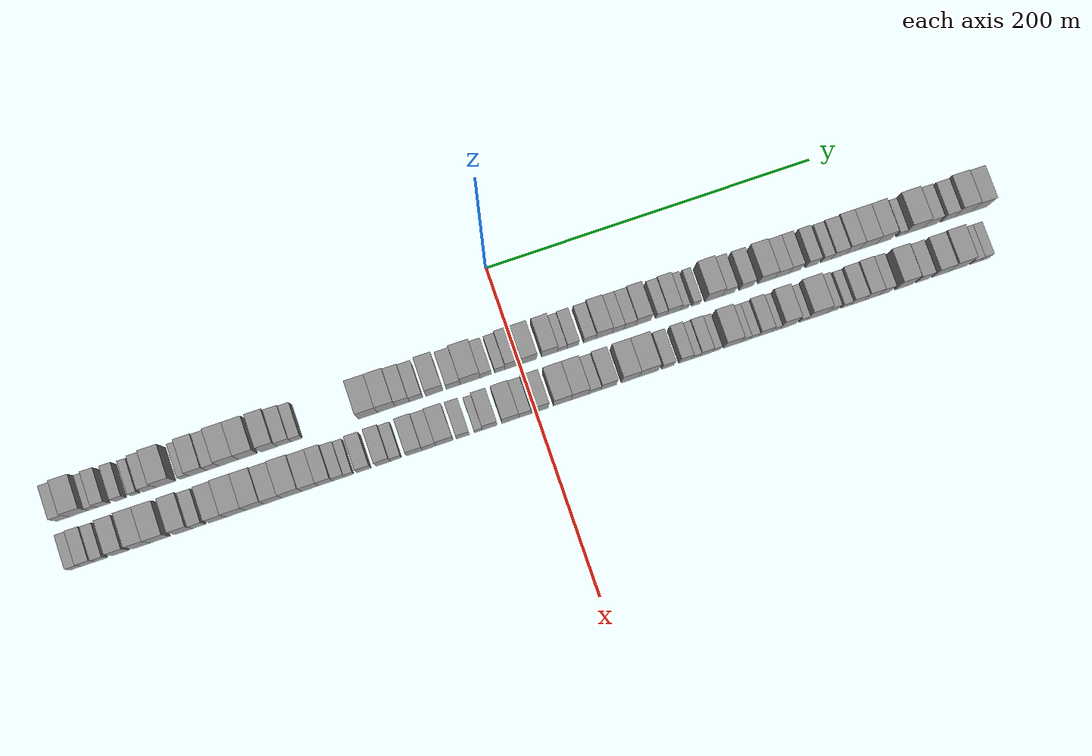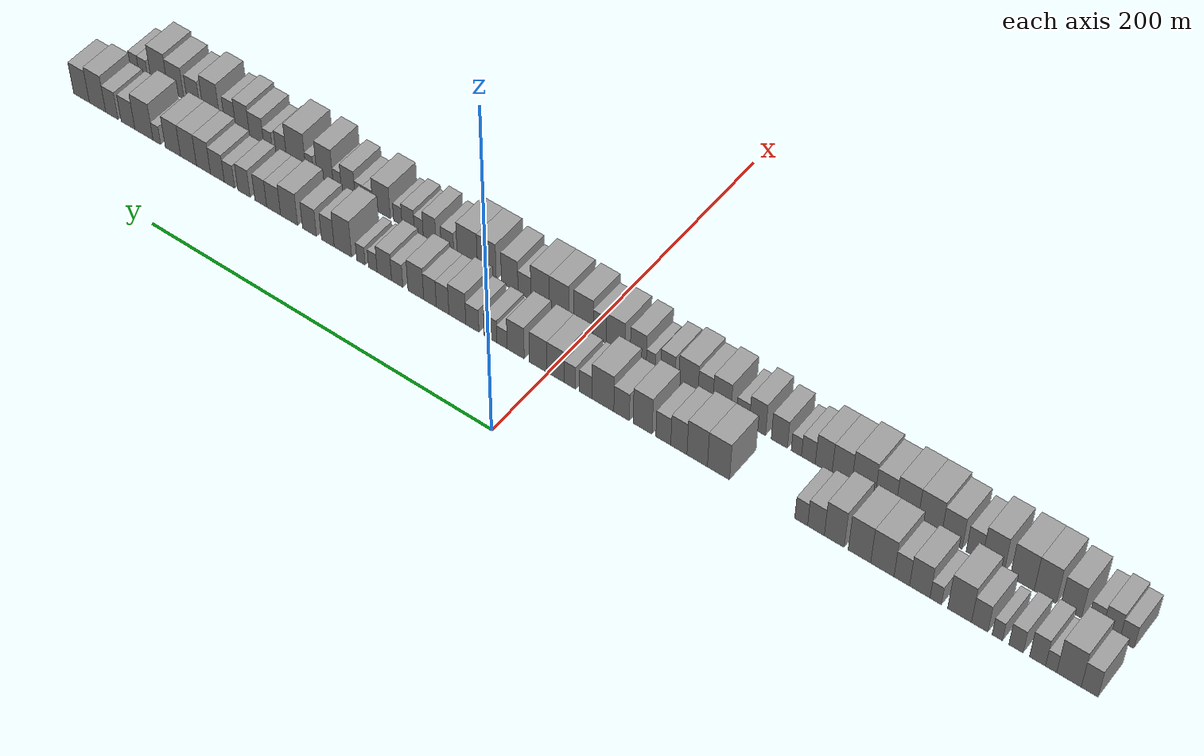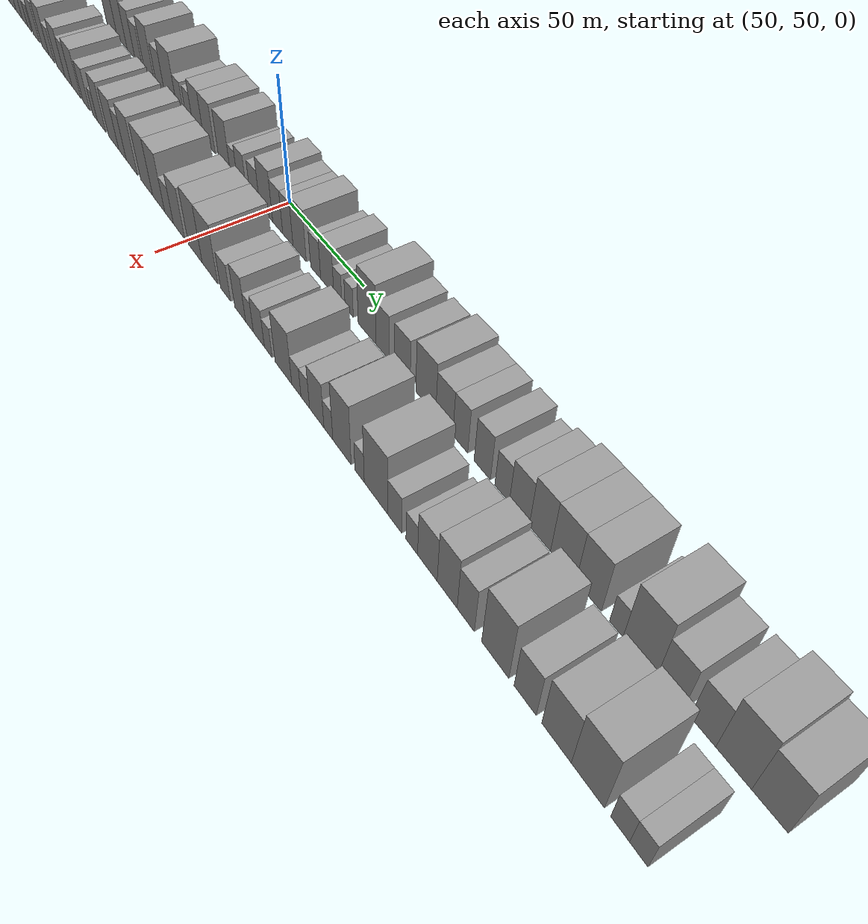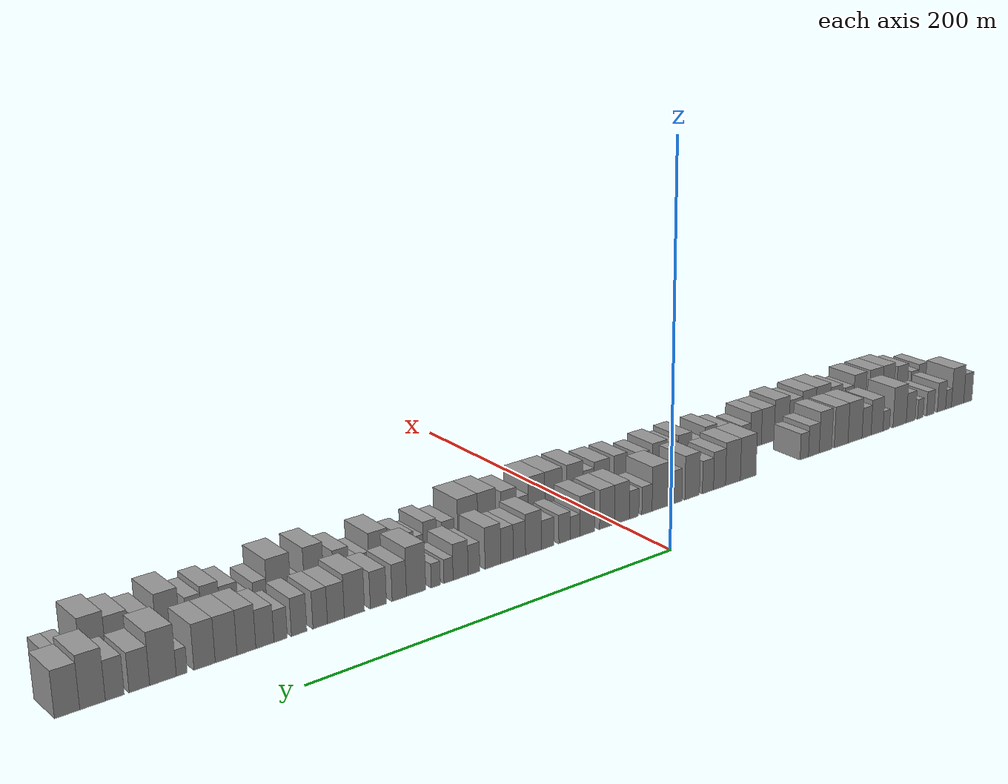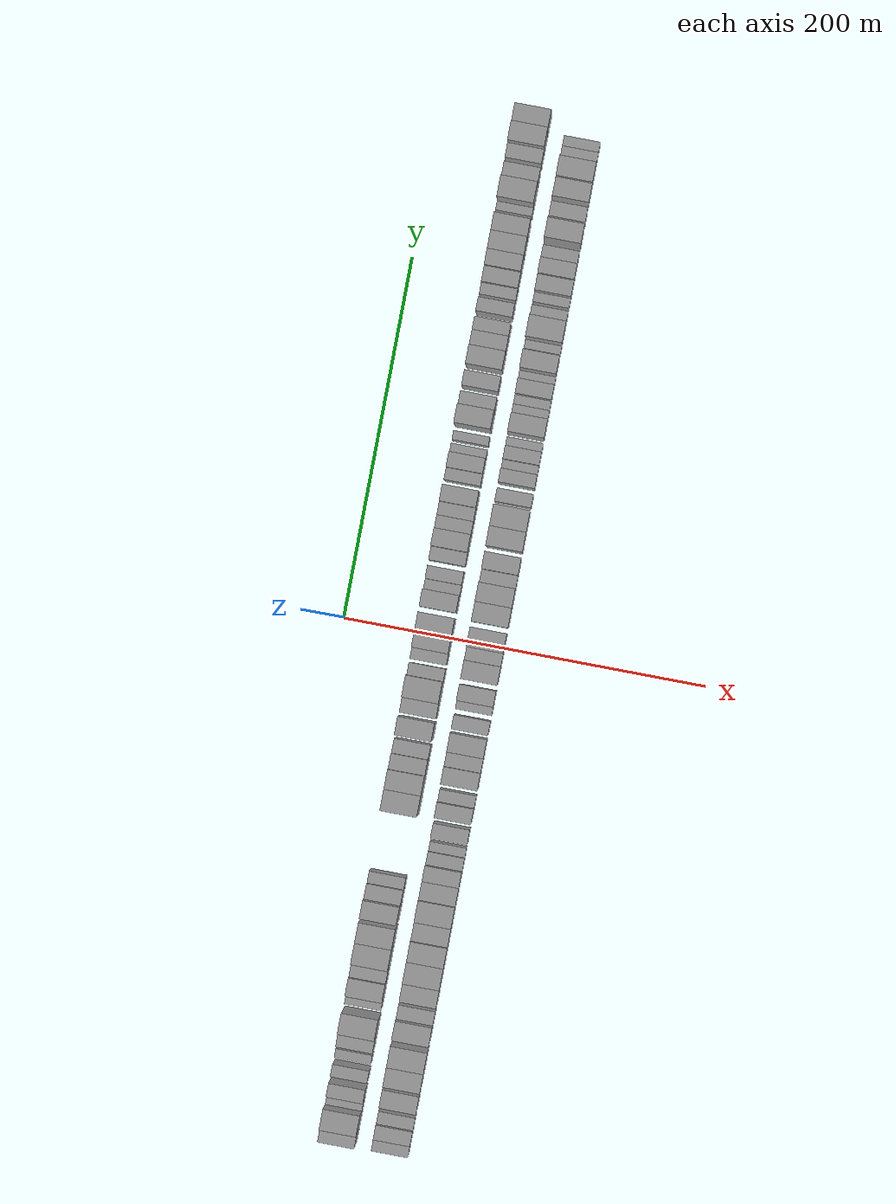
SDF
<sdf version="1.6">
 <world name="default">
  <scene>
   <sky><clouds><speed>12</speed></clouds></sky>
   <ambient>0.4 0.4 0.4 1</ambient>
   <background>0.7 0.7 0.7 1</background>
   <shadows>1</shadows>
  </scene>
  <gravity>0 0 -9.8066</gravity>
  <magnetic_field>6e-06 2.3e-05 -4.2e-05</magnetic_field>
  <physics default="0" name="default_physics" type="ode">
   <ode>
    <solver>
     <type>quick</type>
     <iters>10</iters>
     <sor>1.0</sor>
     <use_dynamic_moi_rescaling>0</use_dynamic_moi_rescaling>
    </solver>
    <constraints>
     <cfm>0</cfm>
     <erp>0.2</erp>
     <contact_max_correcting_vel>100</contact_max_correcting_vel>
     <contact_surface_layer>0.001</contact_surface_layer>
    </constraints>
   </ode>
   <max_step_size>0.004</max_step_size>
   <real_time_factor>1</real_time_factor>
   <real_time_update_rate>250</real_time_update_rate>
  </physics>
  <light name="sun" type="directional">
   <pose>0 0 10 0 0 0</pose>
   <diffuse>0.8 0.8 0.8 1</diffuse>
   <specular>0.2 0.2 0.2 1</specular>
   <attenuation>
    <range>1000</range>
    <constant>0.9</constant>
    <linear>0.01</linear>
    <quadratic>0.001</quadratic>
   </attenuation>
   <direction>-0.5 0.1 -0.9</direction>
  </light>
  <model name="building_1">
   <static>1</static>
   <pose>50.0000 -274.0984 0 0.000000 0.000000 0.000000</pose>
   <link name="link">
    <pose>0 0 9.00 0 0 0</pose>
    <collision name="collision"><geometry><box><size>20.0000 7.8032 18.0000</size></box></geometry></collision>
    <visual name="visual">
     <cast_shadows>0</cast_shadows>
     <geometry><box><size>20.0000 7.8032 18.0000</size></box></geometry>
     <material>
      <script>
       <uri>model://grey_wall/materials/scripts</uri>
       <uri>model://grey_wall/materials/textures</uri>
       <name>vrc/grey_wall</name>
      </script>
     </material>
    </visual>
   </link>
  </model>
  <model name="building_2">
   <static>1</static>
   <pose>50.0000 -264.4991 0 0.000000 0.000000 0.000000</pose>
   <link name="link">
    <pose>0 0 12.00 0 0 0</pose>
    <collision name="collision"><geometry><box><size>20.0000 11.3953 24.0000</size></box></geometry></collision>
    <visual name="visual">
     <cast_shadows>0</cast_shadows>
     <geometry><box><size>20.0000 11.3953 24.0000</size></box></geometry>
     <material>
      <script>
       <uri>model://grey_wall/materials/scripts</uri>
       <uri>model://grey_wall/materials/textures</uri>
       <name>vrc/grey_wall</name>
      </script>
     </material>
    </visual>
   </link>
  </model>
  <model name="building_3">
   <static>1</static>
   <pose>50.0000 -256.1798 0 0.000000 0.000000 0.000000</pose>
   <link name="link">
    <pose>0 0 6.00 0 0 0</pose>
    <collision name="collision"><geometry><box><size>20.0000 5.2434 12.0000</size></box></geometry></collision>
    <visual name="visual">
     <cast_shadows>0</cast_shadows>
     <geometry><box><size>20.0000 5.2434 12.0000</size></box></geometry>
     <material>
      <script>
       <uri>model://grey_wall/materials/scripts</uri>
       <uri>model://grey_wall/materials/textures</uri>
       <name>vrc/grey_wall</name>
      </script>
     </material>
    </visual>
   </link>
  </model>
  <model name="building_4">
   <static>1</static>
   <pose>50.0000 -249.8199 0 0.000000 0.000000 0.000000</pose>
   <link name="link">
    <pose>0 0 9.00 0 0 0</pose>
    <collision name="collision"><geometry><box><size>20.0000 7.4764 18.0000</size></box></geometry></collision>
    <visual name="visual">
     <cast_shadows>0</cast_shadows>
     <geometry><box><size>20.0000 7.4764 18.0000</size></box></geometry>
     <material>
      <script>
       <uri>model://grey_wall/materials/scripts</uri>
       <uri>model://grey_wall/materials/textures</uri>
       <name>vrc/grey_wall</name>
      </script>
     </material>
    </visual>
   </link>
  </model>
  <model name="building_5">
   <static>1</static>
   <pose>50.0000 -239.6976 0 0.000000 0.000000 0.000000</pose>
   <link name="link">
    <pose>0 0 7.50 0 0 0</pose>
    <collision name="collision"><geometry><box><size>20.0000 6.7683 15.0000</size></box></geometry></collision>
    <visual name="visual">
     <cast_shadows>0</cast_shadows>
     <geometry><box><size>20.0000 6.7683 15.0000</size></box></geometry>
     <material>
      <script>
       <uri>model://grey_wall/materials/scripts</uri>
       <uri>model://grey_wall/materials/textures</uri>
       <name>vrc/grey_wall</name>
      </script>
     </material>
    </visual>
   </link>
  </model>
  <model name="building_6">
   <static>1</static>
   <pose>50.0000 -230.8334 0 0.000000 0.000000 0.000000</pose>
   <link name="link">
    <pose>0 0 6.00 0 0 0</pose>
    <collision name="collision"><geometry><box><size>20.0000 4.9600 12.0000</size></box></geometry></collision>
    <visual name="visual">
     <cast_shadows>0</cast_shadows>
     <geometry><box><size>20.0000 4.9600 12.0000</size></box></geometry>
     <material>
      <script>
       <uri>model://grey_wall/materials/scripts</uri>
       <uri>model://grey_wall/materials/textures</uri>
       <name>vrc/grey_wall</name>
      </script>
     </material>
    </visual>
   </link>
  </model>
  <model name="building_7">
   <static>1</static>
   <pose>50.0000 -222.4226 0 0.000000 0.000000 0.000000</pose>
   <link name="link">
    <pose>0 0 9.00 0 0 0</pose>
    <collision name="collision"><geometry><box><size>20.0000 7.8615 18.0000</size></box></geometry></collision>
    <visual name="visual">
     <cast_shadows>0</cast_shadows>
     <geometry><box><size>20.0000 7.8615 18.0000</size></box></geometry>
     <material>
      <script>
       <uri>model://grey_wall/materials/scripts</uri>
       <uri>model://grey_wall/materials/textures</uri>
       <name>vrc/grey_wall</name>
      </script>
     </material>
    </visual>
   </link>
  </model>
  <model name="building_8">
   <static>1</static>
   <pose>50.0000 -212.7386 0 0.000000 0.000000 0.000000</pose>
   <link name="link">
    <pose>0 0 12.00 0 0 0</pose>
    <collision name="collision"><geometry><box><size>20.0000 11.5064 24.0000</size></box></geometry></collision>
    <visual name="visual">
     <cast_shadows>0</cast_shadows>
     <geometry><box><size>20.0000 11.5064 24.0000</size></box></geometry>
     <material>
      <script>
       <uri>model://grey_wall/materials/scripts</uri>
       <uri>model://grey_wall/materials/textures</uri>
       <name>vrc/grey_wall</name>
      </script>
     </material>
    </visual>
   </link>
  </model>
  <model name="building_9">
   <static>1</static>
   <pose>50.0000 -201.2006 0 0.000000 0.000000 0.000000</pose>
   <link name="link">
    <pose>0 0 6.00 0 0 0</pose>
    <collision name="collision"><geometry><box><size>20.0000 5.5696 12.0000</size></box></geometry></collision>
    <visual name="visual">
     <cast_shadows>0</cast_shadows>
     <geometry><box><size>20.0000 5.5696 12.0000</size></box></geometry>
     <material>
      <script>
       <uri>model://grey_wall/materials/scripts</uri>
       <uri>model://grey_wall/materials/textures</uri>
       <name>vrc/grey_wall</name>
      </script>
     </material>
    </visual>
   </link>
  </model>
  <model name="building_10">
   <static>1</static>
   <pose>50.0000 -193.3967 0 0.000000 0.000000 0.000000</pose>
   <link name="link">
    <pose>0 0 10.50 0 0 0</pose>
    <collision name="collision"><geometry><box><size>20.0000 10.0381 21.0000</size></box></geometry></collision>
    <visual name="visual">
     <cast_shadows>0</cast_shadows>
     <geometry><box><size>20.0000 10.0381 21.0000</size></box></geometry>
     <material>
      <script>
       <uri>model://grey_wall/materials/scripts</uri>
       <uri>model://grey_wall/materials/textures</uri>
       <name>vrc/grey_wall</name>
      </script>
     </material>
    </visual>
   </link>
  </model>
  <model name="building_11">
   <static>1</static>
   <pose>50.0000 -184.5823 0 0.000000 0.000000 0.000000</pose>
   <link name="link">
    <pose>0 0 9.00 0 0 0</pose>
    <collision name="collision"><geometry><box><size>20.0000 7.5908 18.0000</size></box></geometry></collision>
    <visual name="visual">
     <cast_shadows>0</cast_shadows>
     <geometry><box><size>20.0000 7.5908 18.0000</size></box></geometry>
     <material>
      <script>
       <uri>model://grey_wall/materials/scripts</uri>
       <uri>model://grey_wall/materials/textures</uri>
       <name>vrc/grey_wall</name>
      </script>
     </material>
    </visual>
   </link>
  </model>
  <model name="building_12">
   <static>1</static>
   <pose>50.0000 -175.0051 0 0.000000 0.000000 0.000000</pose>
   <link name="link">
    <pose>0 0 12.00 0 0 0</pose>
    <collision name="collision"><geometry><box><size>20.0000 11.5636 24.0000</size></box></geometry></collision>
    <visual name="visual">
     <cast_shadows>0</cast_shadows>
     <geometry><box><size>20.0000 11.5636 24.0000</size></box></geometry>
     <material>
      <script>
       <uri>model://grey_wall/materials/scripts</uri>
       <uri>model://grey_wall/materials/textures</uri>
       <name>vrc/grey_wall</name>
      </script>
     </material>
    </visual>
   </link>
  </model>
  <model name="building_13">
   <static>1</static>
   <pose>50.0000 -163.6334 0 0.000000 0.000000 0.000000</pose>
   <link name="link">
    <pose>0 0 12.00 0 0 0</pose>
    <collision name="collision"><geometry><box><size>20.0000 11.1797 24.0000</size></box></geometry></collision>
    <visual name="visual">
     <cast_shadows>0</cast_shadows>
     <geometry><box><size>20.0000 11.1797 24.0000</size></box></geometry>
     <material>
      <script>
       <uri>model://grey_wall/materials/scripts</uri>
       <uri>model://grey_wall/materials/textures</uri>
       <name>vrc/grey_wall</name>
      </script>
     </material>
    </visual>
   </link>
  </model>
  <model name="building_14">
   <static>1</static>
   <pose>50.0000 -151.0319 0 0.000000 0.000000 0.000000</pose>
   <link name="link">
    <pose>0 0 12.00 0 0 0</pose>
    <collision name="collision"><geometry><box><size>20.0000 10.0233 24.0000</size></box></geometry></collision>
    <visual name="visual">
     <cast_shadows>0</cast_shadows>
     <geometry><box><size>20.0000 10.0233 24.0000</size></box></geometry>
     <material>
      <script>
       <uri>model://grey_wall/materials/scripts</uri>
       <uri>model://grey_wall/materials/textures</uri>
       <name>vrc/grey_wall</name>
      </script>
     </material>
    </visual>
   </link>
  </model>
  <model name="building_15">
   <static>1</static>
   <pose>50.0000 -141.7876 0 0.000000 0.000000 0.000000</pose>
   <link name="link">
    <pose>0 0 9.00 0 0 0</pose>
    <collision name="collision"><geometry><box><size>20.0000 8.4652 18.0000</size></box></geometry></collision>
    <visual name="visual">
     <cast_shadows>0</cast_shadows>
     <geometry><box><size>20.0000 8.4652 18.0000</size></box></geometry>
     <material>
      <script>
       <uri>model://grey_wall/materials/scripts</uri>
       <uri>model://grey_wall/materials/textures</uri>
       <name>vrc/grey_wall</name>
      </script>
     </material>
    </visual>
   </link>
  </model>
  <model name="building_16">
   <static>1</static>
   <pose>50.0000 -134.3034 0 0.000000 0.000000 0.000000</pose>
   <link name="link">
    <pose>0 0 7.50 0 0 0</pose>
    <collision name="collision"><geometry><box><size>20.0000 6.5032 15.0000</size></box></geometry></collision>
    <visual name="visual">
     <cast_shadows>0</cast_shadows>
     <geometry><box><size>20.0000 6.5032 15.0000</size></box></geometry>
     <material>
      <script>
       <uri>model://grey_wall/materials/scripts</uri>
       <uri>model://grey_wall/materials/textures</uri>
       <name>vrc/grey_wall</name>
      </script>
     </material>
    </visual>
   </link>
  </model>
  <model name="building_17">
   <static>1</static>
   <pose>50.0000 -91.6437 0 0.000000 0.000000 0.000000</pose>
   <link name="link">
    <pose>0 0 12.00 0 0 0</pose>
    <collision name="collision"><geometry><box><size>20.0000 11.6054 24.0000</size></box></geometry></collision>
    <visual name="visual">
     <cast_shadows>0</cast_shadows>
     <geometry><box><size>20.0000 11.6054 24.0000</size></box></geometry>
     <material>
      <script>
       <uri>model://grey_wall/materials/scripts</uri>
       <uri>model://grey_wall/materials/textures</uri>
       <name>vrc/grey_wall</name>
      </script>
     </material>
    </visual>
   </link>
  </model>
  <model name="building_18">
   <static>1</static>
   <pose>50.0000 -80.4419 0 0.000000 0.000000 0.000000</pose>
   <link name="link">
    <pose>0 0 12.00 0 0 0</pose>
    <collision name="collision"><geometry><box><size>20.0000 10.7983 24.0000</size></box></geometry></collision>
    <visual name="visual">
     <cast_shadows>0</cast_shadows>
     <geometry><box><size>20.0000 10.7983 24.0000</size></box></geometry>
     <material>
      <script>
       <uri>model://grey_wall/materials/scripts</uri>
       <uri>model://grey_wall/materials/textures</uri>
       <name>vrc/grey_wall</name>
      </script>
     </material>
    </visual>
   </link>
  </model>
  <model name="building_19">
   <static>1</static>
   <pose>50.0000 -70.7479 0 0.000000 0.000000 0.000000</pose>
   <link name="link">
    <pose>0 0 10.50 0 0 0</pose>
    <collision name="collision"><geometry><box><size>20.0000 8.5898 21.0000</size></box></geometry></collision>
    <visual name="visual">
     <cast_shadows>0</cast_shadows>
     <geometry><box><size>20.0000 8.5898 21.0000</size></box></geometry>
     <material>
      <script>
       <uri>model://grey_wall/materials/scripts</uri>
       <uri>model://grey_wall/materials/textures</uri>
       <name>vrc/grey_wall</name>
      </script>
     </material>
    </visual>
   </link>
  </model>
  <model name="building_20">
   <static>1</static>
   <pose>50.0000 -62.4788 0 0.000000 0.000000 0.000000</pose>
   <link name="link">
    <pose>0 0 9.00 0 0 0</pose>
    <collision name="collision"><geometry><box><size>20.0000 7.9483 18.0000</size></box></geometry></collision>
    <visual name="visual">
     <cast_shadows>0</cast_shadows>
     <geometry><box><size>20.0000 7.9483 18.0000</size></box></geometry>
     <material>
      <script>
       <uri>model://grey_wall/materials/scripts</uri>
       <uri>model://grey_wall/materials/textures</uri>
       <name>vrc/grey_wall</name>
      </script>
     </material>
    </visual>
   </link>
  </model>
  <model name="building_21">
   <static>1</static>
   <pose>50.0000 -51.3808 0 0.000000 0.000000 0.000000</pose>
   <link name="link">
    <pose>0 0 12.00 0 0 0</pose>
    <collision name="collision"><geometry><box><size>20.0000 10.2478 24.0000</size></box></geometry></collision>
    <visual name="visual">
     <cast_shadows>0</cast_shadows>
     <geometry><box><size>20.0000 10.2478 24.0000</size></box></geometry>
     <material>
      <script>
       <uri>model://grey_wall/materials/scripts</uri>
       <uri>model://grey_wall/materials/textures</uri>
       <name>vrc/grey_wall</name>
      </script>
     </material>
    </visual>
   </link>
  </model>
  <model name="building_22">
   <static>1</static>
   <pose>50.0000 -40.0598 0 0.000000 0.000000 0.000000</pose>
   <link name="link">
    <pose>0 0 9.00 0 0 0</pose>
    <collision name="collision"><geometry><box><size>20.0000 8.3943 18.0000</size></box></geometry></collision>
    <visual name="visual">
     <cast_shadows>0</cast_shadows>
     <geometry><box><size>20.0000 8.3943 18.0000</size></box></geometry>
     <material>
      <script>
       <uri>model://grey_wall/materials/scripts</uri>
       <uri>model://grey_wall/materials/textures</uri>
       <name>vrc/grey_wall</name>
      </script>
     </material>
    </visual>
   </link>
  </model>
  <model name="building_23">
   <static>1</static>
   <pose>50.0000 -29.8732 0 0.000000 0.000000 0.000000</pose>
   <link name="link">
    <pose>0 0 12.00 0 0 0</pose>
    <collision name="collision"><geometry><box><size>20.0000 11.9789 24.0000</size></box></geometry></collision>
    <visual name="visual">
     <cast_shadows>0</cast_shadows>
     <geometry><box><size>20.0000 11.9789 24.0000</size></box></geometry>
     <material>
      <script>
       <uri>model://grey_wall/materials/scripts</uri>
       <uri>model://grey_wall/materials/textures</uri>
       <name>vrc/grey_wall</name>
      </script>
     </material>
    </visual>
   </link>
  </model>
  <model name="building_24">
   <static>1</static>
   <pose>50.0000 -20.4483 0 0.000000 0.000000 0.000000</pose>
   <link name="link">
    <pose>0 0 7.50 0 0 0</pose>
    <collision name="collision"><geometry><box><size>20.0000 6.8708 15.0000</size></box></geometry></collision>
    <visual name="visual">
     <cast_shadows>0</cast_shadows>
     <geometry><box><size>20.0000 6.8708 15.0000</size></box></geometry>
     <material>
      <script>
       <uri>model://grey_wall/materials/scripts</uri>
       <uri>model://grey_wall/materials/textures</uri>
       <name>vrc/grey_wall</name>
      </script>
     </material>
    </visual>
   </link>
  </model>
  <model name="building_25">
   <static>1</static>
   <pose>50.0000 -11.8697 0 0.000000 0.000000 0.000000</pose>
   <link name="link">
    <pose>0 0 7.50 0 0 0</pose>
    <collision name="collision"><geometry><box><size>20.0000 6.2863 15.0000</size></box></geometry></collision>
    <visual name="visual">
     <cast_shadows>0</cast_shadows>
     <geometry><box><size>20.0000 6.2863 15.0000</size></box></geometry>
     <material>
      <script>
       <uri>model://grey_wall/materials/scripts</uri>
       <uri>model://grey_wall/materials/textures</uri>
       <name>vrc/grey_wall</name>
      </script>
     </material>
    </visual>
   </link>
  </model>
  <model name="building_26">
   <static>1</static>
   <pose>50.0000 -3.9226 0 0.000000 0.000000 0.000000</pose>
   <link name="link">
    <pose>0 0 10.50 0 0 0</pose>
    <collision name="collision"><geometry><box><size>20.0000 9.6079 21.0000</size></box></geometry></collision>
    <visual name="visual">
     <cast_shadows>0</cast_shadows>
     <geometry><box><size>20.0000 9.6079 21.0000</size></box></geometry>
     <material>
      <script>
       <uri>model://grey_wall/materials/scripts</uri>
       <uri>model://grey_wall/materials/textures</uri>
       <name>vrc/grey_wall</name>
      </script>
     </material>
    </visual>
   </link>
  </model>
  <model name="building_27">
   <static>1</static>
   <pose>50.0000 5.7127 0 0.000000 0.000000 0.000000</pose>
   <link name="link">
    <pose>0 0 10.50 0 0 0</pose>
    <collision name="collision"><geometry><box><size>20.0000 9.6628 21.0000</size></box></geometry></collision>
    <visual name="visual">
     <cast_shadows>0</cast_shadows>
     <geometry><box><size>20.0000 9.6628 21.0000</size></box></geometry>
     <material>
      <script>
       <uri>model://grey_wall/materials/scripts</uri>
       <uri>model://grey_wall/materials/textures</uri>
       <name>vrc/grey_wall</name>
      </script>
     </material>
    </visual>
   </link>
  </model>
  <model name="building_28">
   <static>1</static>
   <pose>50.0000 18.3281 0 0.000000 0.000000 0.000000</pose>
   <link name="link">
    <pose>0 0 10.50 0 0 0</pose>
    <collision name="collision"><geometry><box><size>20.0000 9.5679 21.0000</size></box></geometry></collision>
    <visual name="visual">
     <cast_shadows>0</cast_shadows>
     <geometry><box><size>20.0000 9.5679 21.0000</size></box></geometry>
     <material>
      <script>
       <uri>model://grey_wall/materials/scripts</uri>
       <uri>model://grey_wall/materials/textures</uri>
       <name>vrc/grey_wall</name>
      </script>
     </material>
    </visual>
   </link>
  </model>
  <model name="building_29">
   <static>1</static>
   <pose>50.0000 26.0019 0 0.000000 0.000000 0.000000</pose>
   <link name="link">
    <pose>0 0 6.00 0 0 0</pose>
    <collision name="collision"><geometry><box><size>20.0000 5.7797 12.0000</size></box></geometry></collision>
    <visual name="visual">
     <cast_shadows>0</cast_shadows>
     <geometry><box><size>20.0000 5.7797 12.0000</size></box></geometry>
     <material>
      <script>
       <uri>model://grey_wall/materials/scripts</uri>
       <uri>model://grey_wall/materials/textures</uri>
       <name>vrc/grey_wall</name>
      </script>
     </material>
    </visual>
   </link>
  </model>
  <model name="building_30">
   <static>1</static>
   <pose>50.0000 32.5020 0 0.000000 0.000000 0.000000</pose>
   <link name="link">
    <pose>0 0 7.50 0 0 0</pose>
    <collision name="collision"><geometry><box><size>20.0000 7.2206 15.0000</size></box></geometry></collision>
    <visual name="visual">
     <cast_shadows>0</cast_shadows>
     <geometry><box><size>20.0000 7.2206 15.0000</size></box></geometry>
     <material>
      <script>
       <uri>model://grey_wall/materials/scripts</uri>
       <uri>model://grey_wall/materials/textures</uri>
       <name>vrc/grey_wall</name>
      </script>
     </material>
    </visual>
   </link>
  </model>
  <model name="building_31">
   <static>1</static>
   <pose>50.0000 42.8494 0 0.000000 0.000000 0.000000</pose>
   <link name="link">
    <pose>0 0 7.50 0 0 0</pose>
    <collision name="collision"><geometry><box><size>20.0000 7.4743 15.0000</size></box></geometry></collision>
    <visual name="visual">
     <cast_shadows>0</cast_shadows>
     <geometry><box><size>20.0000 7.4743 15.0000</size></box></geometry>
     <material>
      <script>
       <uri>model://grey_wall/materials/scripts</uri>
       <uri>model://grey_wall/materials/textures</uri>
       <name>vrc/grey_wall</name>
      </script>
     </material>
    </visual>
   </link>
  </model>
  <model name="building_32">
   <static>1</static>
   <pose>50.0000 51.4524 0 0.000000 0.000000 0.000000</pose>
   <link name="link">
    <pose>0 0 10.50 0 0 0</pose>
    <collision name="collision"><geometry><box><size>20.0000 9.7316 21.0000</size></box></geometry></collision>
    <visual name="visual">
     <cast_shadows>0</cast_shadows>
     <geometry><box><size>20.0000 9.7316 21.0000</size></box></geometry>
     <material>
      <script>
       <uri>model://grey_wall/materials/scripts</uri>
       <uri>model://grey_wall/materials/textures</uri>
       <name>vrc/grey_wall</name>
      </script>
     </material>
    </visual>
   </link>
  </model>
  <model name="building_33">
   <static>1</static>
   <pose>50.0000 59.9531 0 0.000000 0.000000 0.000000</pose>
   <link name="link">
    <pose>0 0 9.00 0 0 0</pose>
    <collision name="collision"><geometry><box><size>20.0000 7.2698 18.0000</size></box></geometry></collision>
    <visual name="visual">
     <cast_shadows>0</cast_shadows>
     <geometry><box><size>20.0000 7.2698 18.0000</size></box></geometry>
     <material>
      <script>
       <uri>model://grey_wall/materials/scripts</uri>
       <uri>model://grey_wall/materials/textures</uri>
       <name>vrc/grey_wall</name>
      </script>
     </material>
    </visual>
   </link>
  </model>
  <model name="building_34">
   <static>1</static>
   <pose>50.0000 67.2421 0 0.000000 0.000000 0.000000</pose>
   <link name="link">
    <pose>0 0 9.00 0 0 0</pose>
    <collision name="collision"><geometry><box><size>20.0000 7.3082 18.0000</size></box></geometry></collision>
    <visual name="visual">
     <cast_shadows>0</cast_shadows>
     <geometry><box><size>20.0000 7.3082 18.0000</size></box></geometry>
     <material>
      <script>
       <uri>model://grey_wall/materials/scripts</uri>
       <uri>model://grey_wall/materials/textures</uri>
       <name>vrc/grey_wall</name>
      </script>
     </material>
    </visual>
   </link>
  </model>
  <model name="building_35">
   <static>1</static>
   <pose>50.0000 75.4865 0 0.000000 0.000000 0.000000</pose>
   <link name="link">
    <pose>0 0 10.50 0 0 0</pose>
    <collision name="collision"><geometry><box><size>20.0000 9.1805 21.0000</size></box></geometry></collision>
    <visual name="visual">
     <cast_shadows>0</cast_shadows>
     <geometry><box><size>20.0000 9.1805 21.0000</size></box></geometry>
     <material>
      <script>
       <uri>model://grey_wall/materials/scripts</uri>
       <uri>model://grey_wall/materials/textures</uri>
       <name>vrc/grey_wall</name>
      </script>
     </material>
    </visual>
   </link>
  </model>
  <model name="building_36">
   <static>1</static>
   <pose>50.0000 86.3893 0 0.000000 0.000000 0.000000</pose>
   <link name="link">
    <pose>0 0 7.50 0 0 0</pose>
    <collision name="collision"><geometry><box><size>20.0000 6.6253 15.0000</size></box></geometry></collision>
    <visual name="visual">
     <cast_shadows>0</cast_shadows>
     <geometry><box><size>20.0000 6.6253 15.0000</size></box></geometry>
     <material>
      <script>
       <uri>model://grey_wall/materials/scripts</uri>
       <uri>model://grey_wall/materials/textures</uri>
       <name>vrc/grey_wall</name>
      </script>
     </material>
    </visual>
   </link>
  </model>
  <model name="building_37">
   <static>1</static>
   <pose>50.0000 93.9520 0 0.000000 0.000000 0.000000</pose>
   <link name="link">
    <pose>0 0 9.00 0 0 0</pose>
    <collision name="collision"><geometry><box><size>20.0000 8.5001 18.0000</size></box></geometry></collision>
    <visual name="visual">
     <cast_shadows>0</cast_shadows>
     <geometry><box><size>20.0000 8.5001 18.0000</size></box></geometry>
     <material>
      <script>
       <uri>model://grey_wall/materials/scripts</uri>
       <uri>model://grey_wall/materials/textures</uri>
       <name>vrc/grey_wall</name>
      </script>
     </material>
    </visual>
   </link>
  </model>
  <model name="building_38">
   <static>1</static>
   <pose>50.0000 100.7623 0 0.000000 0.000000 0.000000</pose>
   <link name="link">
    <pose>0 0 6.00 0 0 0</pose>
    <collision name="collision"><geometry><box><size>20.0000 5.1205 12.0000</size></box></geometry></collision>
    <visual name="visual">
     <cast_shadows>0</cast_shadows>
     <geometry><box><size>20.0000 5.1205 12.0000</size></box></geometry>
     <material>
      <script>
       <uri>model://grey_wall/materials/scripts</uri>
       <uri>model://grey_wall/materials/textures</uri>
       <name>vrc/grey_wall</name>
      </script>
     </material>
    </visual>
   </link>
  </model>
  <model name="building_39">
   <static>1</static>
   <pose>50.0000 107.8391 0 0.000000 0.000000 0.000000</pose>
   <link name="link">
    <pose>0 0 6.00 0 0 0</pose>
    <collision name="collision"><geometry><box><size>20.0000 5.0329 12.0000</size></box></geometry></collision>
    <visual name="visual">
     <cast_shadows>0</cast_shadows>
     <geometry><box><size>20.0000 5.0329 12.0000</size></box></geometry>
     <material>
      <script>
       <uri>model://grey_wall/materials/scripts</uri>
       <uri>model://grey_wall/materials/textures</uri>
       <name>vrc/grey_wall</name>
      </script>
     </material>
    </visual>
   </link>
  </model>
  <model name="building_40">
   <static>1</static>
   <pose>50.0000 118.5804 0 0.000000 0.000000 0.000000</pose>
   <link name="link">
    <pose>0 0 12.00 0 0 0</pose>
    <collision name="collision"><geometry><box><size>20.0000 10.4498 24.0000</size></box></geometry></collision>
    <visual name="visual">
     <cast_shadows>0</cast_shadows>
     <geometry><box><size>20.0000 10.4498 24.0000</size></box></geometry>
     <material>
      <script>
       <uri>model://grey_wall/materials/scripts</uri>
       <uri>model://grey_wall/materials/textures</uri>
       <name>vrc/grey_wall</name>
      </script>
     </material>
    </visual>
   </link>
  </model>
  <model name="building_41">
   <static>1</static>
   <pose>50.0000 127.6384 0 0.000000 0.000000 0.000000</pose>
   <link name="link">
    <pose>0 0 9.00 0 0 0</pose>
    <collision name="collision"><geometry><box><size>20.0000 7.6661 18.0000</size></box></geometry></collision>
    <visual name="visual">
     <cast_shadows>0</cast_shadows>
     <geometry><box><size>20.0000 7.6661 18.0000</size></box></geometry>
     <material>
      <script>
       <uri>model://grey_wall/materials/scripts</uri>
       <uri>model://grey_wall/materials/textures</uri>
       <name>vrc/grey_wall</name>
      </script>
     </material>
    </visual>
   </link>
  </model>
  <model name="building_42">
   <static>1</static>
   <pose>50.0000 138.7081 0 0.000000 0.000000 0.000000</pose>
   <link name="link">
    <pose>0 0 9.00 0 0 0</pose>
    <collision name="collision"><geometry><box><size>20.0000 8.4734 18.0000</size></box></geometry></collision>
    <visual name="visual">
     <cast_shadows>0</cast_shadows>
     <geometry><box><size>20.0000 8.4734 18.0000</size></box></geometry>
     <material>
      <script>
       <uri>model://grey_wall/materials/scripts</uri>
       <uri>model://grey_wall/materials/textures</uri>
       <name>vrc/grey_wall</name>
      </script>
     </material>
    </visual>
   </link>
  </model>
  <model name="building_43">
   <static>1</static>
   <pose>50.0000 151.1465 0 0.000000 0.000000 0.000000</pose>
   <link name="link">
    <pose>0 0 10.50 0 0 0</pose>
    <collision name="collision"><geometry><box><size>20.0000 10.4034 21.0000</size></box></geometry></collision>
    <visual name="visual">
     <cast_shadows>0</cast_shadows>
     <geometry><box><size>20.0000 10.4034 21.0000</size></box></geometry>
     <material>
      <script>
       <uri>model://grey_wall/materials/scripts</uri>
       <uri>model://grey_wall/materials/textures</uri>
       <name>vrc/grey_wall</name>
      </script>
     </material>
    </visual>
   </link>
  </model>
  <model name="building_44">
   <static>1</static>
   <pose>50.0000 160.6406 0 0.000000 0.000000 0.000000</pose>
   <link name="link">
    <pose>0 0 9.00 0 0 0</pose>
    <collision name="collision"><geometry><box><size>20.0000 8.5848 18.0000</size></box></geometry></collision>
    <visual name="visual">
     <cast_shadows>0</cast_shadows>
     <geometry><box><size>20.0000 8.5848 18.0000</size></box></geometry>
     <material>
      <script>
       <uri>model://grey_wall/materials/scripts</uri>
       <uri>model://grey_wall/materials/textures</uri>
       <name>vrc/grey_wall</name>
      </script>
     </material>
    </visual>
   </link>
  </model>
  <model name="building_45">
   <static>1</static>
   <pose>50.0000 168.5676 0 0.000000 0.000000 0.000000</pose>
   <link name="link">
    <pose>0 0 9.00 0 0 0</pose>
    <collision name="collision"><geometry><box><size>20.0000 7.2692 18.0000</size></box></geometry></collision>
    <visual name="visual">
     <cast_shadows>0</cast_shadows>
     <geometry><box><size>20.0000 7.2692 18.0000</size></box></geometry>
     <material>
      <script>
       <uri>model://grey_wall/materials/scripts</uri>
       <uri>model://grey_wall/materials/textures</uri>
       <name>vrc/grey_wall</name>
      </script>
     </material>
    </visual>
   </link>
  </model>
  <model name="building_46">
   <static>1</static>
   <pose>50.0000 179.0036 0 0.000000 0.000000 0.000000</pose>
   <link name="link">
    <pose>0 0 9.00 0 0 0</pose>
    <collision name="collision"><geometry><box><size>20.0000 7.6027 18.0000</size></box></geometry></collision>
    <visual name="visual">
     <cast_shadows>0</cast_shadows>
     <geometry><box><size>20.0000 7.6027 18.0000</size></box></geometry>
     <material>
      <script>
       <uri>model://grey_wall/materials/scripts</uri>
       <uri>model://grey_wall/materials/textures</uri>
       <name>vrc/grey_wall</name>
      </script>
     </material>
    </visual>
   </link>
  </model>
  <model name="building_47">
   <static>1</static>
   <pose>50.0000 188.0357 0 0.000000 0.000000 0.000000</pose>
   <link name="link">
    <pose>0 0 7.50 0 0 0</pose>
    <collision name="collision"><geometry><box><size>20.0000 6.4615 15.0000</size></box></geometry></collision>
    <visual name="visual">
     <cast_shadows>0</cast_shadows>
     <geometry><box><size>20.0000 6.4615 15.0000</size></box></geometry>
     <material>
      <script>
       <uri>model://grey_wall/materials/scripts</uri>
       <uri>model://grey_wall/materials/textures</uri>
       <name>vrc/grey_wall</name>
      </script>
     </material>
    </visual>
   </link>
  </model>
  <model name="building_48">
   <static>1</static>
   <pose>50.0000 195.5984 0 0.000000 0.000000 0.000000</pose>
   <link name="link">
    <pose>0 0 9.00 0 0 0</pose>
    <collision name="collision"><geometry><box><size>20.0000 8.6639 18.0000</size></box></geometry></collision>
    <visual name="visual">
     <cast_shadows>0</cast_shadows>
     <geometry><box><size>20.0000 8.6639 18.0000</size></box></geometry>
     <material>
      <script>
       <uri>model://grey_wall/materials/scripts</uri>
       <uri>model://grey_wall/materials/textures</uri>
       <name>vrc/grey_wall</name>
      </script>
     </material>
    </visual>
   </link>
  </model>
  <model name="building_49">
   <static>1</static>
   <pose>50.0000 204.3596 0 0.000000 0.000000 0.000000</pose>
   <link name="link">
    <pose>0 0 10.50 0 0 0</pose>
    <collision name="collision"><geometry><box><size>20.0000 8.8585 21.0000</size></box></geometry></collision>
    <visual name="visual">
     <cast_shadows>0</cast_shadows>
     <geometry><box><size>20.0000 8.8585 21.0000</size></box></geometry>
     <material>
      <script>
       <uri>model://grey_wall/materials/scripts</uri>
       <uri>model://grey_wall/materials/textures</uri>
       <name>vrc/grey_wall</name>
      </script>
     </material>
    </visual>
   </link>
  </model>
  <model name="building_50">
   <static>1</static>
   <pose>50.0000 213.8407 0 0.000000 0.000000 0.000000</pose>
   <link name="link">
    <pose>0 0 10.50 0 0 0</pose>
    <collision name="collision"><geometry><box><size>20.0000 10.1037 21.0000</size></box></geometry></collision>
    <visual name="visual">
     <cast_shadows>0</cast_shadows>
     <geometry><box><size>20.0000 10.1037 21.0000</size></box></geometry>
     <material>
      <script>
       <uri>model://grey_wall/materials/scripts</uri>
       <uri>model://grey_wall/materials/textures</uri>
       <name>vrc/grey_wall</name>
      </script>
     </material>
    </visual>
   </link>
  </model>
  <model name="building_51">
   <static>1</static>
   <pose>50.0000 223.7538 0 0.000000 0.000000 0.000000</pose>
   <link name="link">
    <pose>0 0 10.50 0 0 0</pose>
    <collision name="collision"><geometry><box><size>20.0000 9.7225 21.0000</size></box></geometry></collision>
    <visual name="visual">
     <cast_shadows>0</cast_shadows>
     <geometry><box><size>20.0000 9.7225 21.0000</size></box></geometry>
     <material>
      <script>
       <uri>model://grey_wall/materials/scripts</uri>
       <uri>model://grey_wall/materials/textures</uri>
       <name>vrc/grey_wall</name>
      </script>
     </material>
    </visual>
   </link>
  </model>
  <model name="building_52">
   <static>1</static>
   <pose>50.0000 234.0645 0 0.000000 0.000000 0.000000</pose>
   <link name="link">
    <pose>0 0 6.00 0 0 0</pose>
    <collision name="collision"><geometry><box><size>20.0000 4.8989 12.0000</size></box></geometry></collision>
    <visual name="visual">
     <cast_shadows>0</cast_shadows>
     <geometry><box><size>20.0000 4.8989 12.0000</size></box></geometry>
     <material>
      <script>
       <uri>model://grey_wall/materials/scripts</uri>
       <uri>model://grey_wall/materials/textures</uri>
       <name>vrc/grey_wall</name>
      </script>
     </material>
    </visual>
   </link>
  </model>
  <model name="building_53">
   <static>1</static>
   <pose>50.0000 242.3845 0 0.000000 0.000000 0.000000</pose>
   <link name="link">
    <pose>0 0 12.00 0 0 0</pose>
    <collision name="collision"><geometry><box><size>20.0000 11.7411 24.0000</size></box></geometry></collision>
    <visual name="visual">
     <cast_shadows>0</cast_shadows>
     <geometry><box><size>20.0000 11.7411 24.0000</size></box></geometry>
     <material>
      <script>
       <uri>model://grey_wall/materials/scripts</uri>
       <uri>model://grey_wall/materials/textures</uri>
       <name>vrc/grey_wall</name>
      </script>
     </material>
    </visual>
   </link>
  </model>
  <model name="building_54">
   <static>1</static>
   <pose>50.0000 252.7327 0 0.000000 0.000000 0.000000</pose>
   <link name="link">
    <pose>0 0 9.00 0 0 0</pose>
    <collision name="collision"><geometry><box><size>20.0000 8.9555 18.0000</size></box></geometry></collision>
    <visual name="visual">
     <cast_shadows>0</cast_shadows>
     <geometry><box><size>20.0000 8.9555 18.0000</size></box></geometry>
     <material>
      <script>
       <uri>model://grey_wall/materials/scripts</uri>
       <uri>model://grey_wall/materials/textures</uri>
       <name>vrc/grey_wall</name>
      </script>
     </material>
    </visual>
   </link>
  </model>
  <model name="building_55">
   <static>1</static>
   <pose>50.0000 263.2553 0 0.000000 0.000000 0.000000</pose>
   <link name="link">
    <pose>0 0 9.00 0 0 0</pose>
    <collision name="collision"><geometry><box><size>20.0000 8.0896 18.0000</size></box></geometry></collision>
    <visual name="visual">
     <cast_shadows>0</cast_shadows>
     <geometry><box><size>20.0000 8.0896 18.0000</size></box></geometry>
     <material>
      <script>
       <uri>model://grey_wall/materials/scripts</uri>
       <uri>model://grey_wall/materials/textures</uri>
       <name>vrc/grey_wall</name>
      </script>
     </material>
    </visual>
   </link>
  </model>
  <model name="building_56">
   <static>1</static>
   <pose>50.0000 272.6476 0 0.000000 0.000000 0.000000</pose>
   <link name="link">
    <pose>0 0 12.00 0 0 0</pose>
    <collision name="collision"><geometry><box><size>20.0000 10.6950 24.0000</size></box></geometry></collision>
    <visual name="visual">
     <cast_shadows>0</cast_shadows>
     <geometry><box><size>20.0000 10.6950 24.0000</size></box></geometry>
     <material>
      <script>
       <uri>model://grey_wall/materials/scripts</uri>
       <uri>model://grey_wall/materials/textures</uri>
       <name>vrc/grey_wall</name>
      </script>
     </material>
    </visual>
   </link>
  </model>
  <model name="building_57">
   <static>1</static>
   <pose>50.0000 283.1999 0 0.000000 0.000000 0.000000</pose>
   <link name="link">
    <pose>0 0 10.50 0 0 0</pose>
    <collision name="collision"><geometry><box><size>20.0000 10.4095 21.0000</size></box></geometry></collision>
    <visual name="visual">
     <cast_shadows>0</cast_shadows>
     <geometry><box><size>20.0000 10.4095 21.0000</size></box></geometry>
     <material>
      <script>
       <uri>model://grey_wall/materials/scripts</uri>
       <uri>model://grey_wall/materials/textures</uri>
       <name>vrc/grey_wall</name>
      </script>
     </material>
    </visual>
   </link>
  </model>
  <model name="building_58">
   <static>1</static>
   <pose>79.0000 -274.6363 0 0.000000 0.000000 0.000000</pose>
   <link name="link">
    <pose>0 0 7.50 0 0 0</pose>
    <collision name="collision"><geometry><box><size>20.0000 6.7274 15.0000</size></box></geometry></collision>
    <visual name="visual">
     <cast_shadows>0</cast_shadows>
     <geometry><box><size>20.0000 6.7274 15.0000</size></box></geometry>
     <material>
      <script>
       <uri>model://grey_wall/materials/scripts</uri>
       <uri>model://grey_wall/materials/textures</uri>
       <name>vrc/grey_wall</name>
      </script>
     </material>
    </visual>
   </link>
  </model>
  <model name="building_59">
   <static>1</static>
   <pose>79.0000 -267.2774 0 0.000000 0.000000 0.000000</pose>
   <link name="link">
    <pose>0 0 9.00 0 0 0</pose>
    <collision name="collision"><geometry><box><size>20.0000 7.9905 18.0000</size></box></geometry></collision>
    <visual name="visual">
     <cast_shadows>0</cast_shadows>
     <geometry><box><size>20.0000 7.9905 18.0000</size></box></geometry>
     <material>
      <script>
       <uri>model://grey_wall/materials/scripts</uri>
       <uri>model://grey_wall/materials/textures</uri>
       <name>vrc/grey_wall</name>
      </script>
     </material>
    </visual>
   </link>
  </model>
  <model name="building_60">
   <static>1</static>
   <pose>79.0000 -259.8682 0 0.000000 0.000000 0.000000</pose>
   <link name="link">
    <pose>0 0 7.50 0 0 0</pose>
    <collision name="collision"><geometry><box><size>20.0000 6.8278 15.0000</size></box></geometry></collision>
    <visual name="visual">
     <cast_shadows>0</cast_shadows>
     <geometry><box><size>20.0000 6.8278 15.0000</size></box></geometry>
     <material>
      <script>
       <uri>model://grey_wall/materials/scripts</uri>
       <uri>model://grey_wall/materials/textures</uri>
       <name>vrc/grey_wall</name>
      </script>
     </material>
    </visual>
   </link>
  </model>
  <model name="building_61">
   <static>1</static>
   <pose>79.0000 -248.5014 0 0.000000 0.000000 0.000000</pose>
   <link name="link">
    <pose>0 0 10.50 0 0 0</pose>
    <collision name="collision"><geometry><box><size>20.0000 9.9060 21.0000</size></box></geometry></collision>
    <visual name="visual">
     <cast_shadows>0</cast_shadows>
     <geometry><box><size>20.0000 9.9060 21.0000</size></box></geometry>
     <material>
      <script>
       <uri>model://grey_wall/materials/scripts</uri>
       <uri>model://grey_wall/materials/textures</uri>
       <name>vrc/grey_wall</name>
      </script>
     </material>
    </visual>
   </link>
  </model>
  <model name="building_62">
   <static>1</static>
   <pose>79.0000 -236.2479 0 0.000000 0.000000 0.000000</pose>
   <link name="link">
    <pose>0 0 12.00 0 0 0</pose>
    <collision name="collision"><geometry><box><size>20.0000 10.6009 24.0000</size></box></geometry></collision>
    <visual name="visual">
     <cast_shadows>0</cast_shadows>
     <geometry><box><size>20.0000 10.6009 24.0000</size></box></geometry>
     <material>
      <script>
       <uri>model://grey_wall/materials/scripts</uri>
       <uri>model://grey_wall/materials/textures</uri>
       <name>vrc/grey_wall</name>
      </script>
     </material>
    </visual>
   </link>
  </model>
  <model name="building_63">
   <static>1</static>
   <pose>79.0000 -225.1580 0 0.000000 0.000000 0.000000</pose>
   <link name="link">
    <pose>0 0 12.00 0 0 0</pose>
    <collision name="collision"><geometry><box><size>20.0000 11.5790 24.0000</size></box></geometry></collision>
    <visual name="visual">
     <cast_shadows>0</cast_shadows>
     <geometry><box><size>20.0000 11.5790 24.0000</size></box></geometry>
     <material>
      <script>
       <uri>model://grey_wall/materials/scripts</uri>
       <uri>model://grey_wall/materials/textures</uri>
       <name>vrc/grey_wall</name>
      </script>
     </material>
    </visual>
   </link>
  </model>
  <model name="building_64">
   <static>1</static>
   <pose>79.0000 -211.0522 0 0.000000 0.000000 0.000000</pose>
   <link name="link">
    <pose>0 0 12.00 0 0 0</pose>
    <collision name="collision"><geometry><box><size>20.0000 10.6325 24.0000</size></box></geometry></collision>
    <visual name="visual">
     <cast_shadows>0</cast_shadows>
     <geometry><box><size>20.0000 10.6325 24.0000</size></box></geometry>
     <material>
      <script>
       <uri>model://grey_wall/materials/scripts</uri>
       <uri>model://grey_wall/materials/textures</uri>
       <name>vrc/grey_wall</name>
      </script>
     </material>
    </visual>
   </link>
  </model>
  <model name="building_65">
   <static>1</static>
   <pose>79.0000 -201.8624 0 0.000000 0.000000 0.000000</pose>
   <link name="link">
    <pose>0 0 9.00 0 0 0</pose>
    <collision name="collision"><geometry><box><size>20.0000 7.7469 18.0000</size></box></geometry></collision>
    <visual name="visual">
     <cast_shadows>0</cast_shadows>
     <geometry><box><size>20.0000 7.7469 18.0000</size></box></geometry>
     <material>
      <script>
       <uri>model://grey_wall/materials/scripts</uri>
       <uri>model://grey_wall/materials/textures</uri>
       <name>vrc/grey_wall</name>
      </script>
     </material>
    </visual>
   </link>
  </model>
  <model name="building_66">
   <static>1</static>
   <pose>79.0000 -190.8529 0 0.000000 0.000000 0.000000</pose>
   <link name="link">
    <pose>0 0 10.50 0 0 0</pose>
    <collision name="collision"><geometry><box><size>20.0000 10.2721 21.0000</size></box></geometry></collision>
    <visual name="visual">
     <cast_shadows>0</cast_shadows>
     <geometry><box><size>20.0000 10.2721 21.0000</size></box></geometry>
     <material>
      <script>
       <uri>model://grey_wall/materials/scripts</uri>
       <uri>model://grey_wall/materials/textures</uri>
       <name>vrc/grey_wall</name>
      </script>
     </material>
    </visual>
   </link>
  </model>
  <model name="building_67">
   <static>1</static>
   <pose>79.0000 -179.8045 0 0.000000 0.000000 0.000000</pose>
   <link name="link">
    <pose>0 0 12.00 0 0 0</pose>
    <collision name="collision"><geometry><box><size>20.0000 11.8248 24.0000</size></box></geometry></collision>
    <visual name="visual">
     <cast_shadows>0</cast_shadows>
     <geometry><box><size>20.0000 11.8248 24.0000</size></box></geometry>
     <material>
      <script>
       <uri>model://grey_wall/materials/scripts</uri>
       <uri>model://grey_wall/materials/textures</uri>
       <name>vrc/grey_wall</name>
      </script>
     </material>
    </visual>
   </link>
  </model>
  <model name="building_68">
   <static>1</static>
   <pose>79.0000 -168.3665 0 0.000000 0.000000 0.000000</pose>
   <link name="link">
    <pose>0 0 12.00 0 0 0</pose>
    <collision name="collision"><geometry><box><size>20.0000 11.0511 24.0000</size></box></geometry></collision>
    <visual name="visual">
     <cast_shadows>0</cast_shadows>
     <geometry><box><size>20.0000 11.0511 24.0000</size></box></geometry>
     <material>
      <script>
       <uri>model://grey_wall/materials/scripts</uri>
       <uri>model://grey_wall/materials/textures</uri>
       <name>vrc/grey_wall</name>
      </script>
     </material>
    </visual>
   </link>
  </model>
  <model name="building_69">
   <static>1</static>
   <pose>79.0000 -157.6534 0 0.000000 0.000000 0.000000</pose>
   <link name="link">
    <pose>0 0 10.50 0 0 0</pose>
    <collision name="collision"><geometry><box><size>20.0000 10.3751 21.0000</size></box></geometry></collision>
    <visual name="visual">
     <cast_shadows>0</cast_shadows>
     <geometry><box><size>20.0000 10.3751 21.0000</size></box></geometry>
     <material>
      <script>
       <uri>model://grey_wall/materials/scripts</uri>
       <uri>model://grey_wall/materials/textures</uri>
       <name>vrc/grey_wall</name>
      </script>
     </material>
    </visual>
   </link>
  </model>
  <model name="building_70">
   <static>1</static>
   <pose>79.0000 -146.5816 0 0.000000 0.000000 0.000000</pose>
   <link name="link">
    <pose>0 0 12.00 0 0 0</pose>
    <collision name="collision"><geometry><box><size>20.0000 11.7685 24.0000</size></box></geometry></collision>
    <visual name="visual">
     <cast_shadows>0</cast_shadows>
     <geometry><box><size>20.0000 11.7685 24.0000</size></box></geometry>
     <material>
      <script>
       <uri>model://grey_wall/materials/scripts</uri>
       <uri>model://grey_wall/materials/textures</uri>
       <name>vrc/grey_wall</name>
      </script>
     </material>
    </visual>
   </link>
  </model>
  <model name="building_71">
   <static>1</static>
   <pose>79.0000 -135.6653 0 0.000000 0.000000 0.000000</pose>
   <link name="link">
    <pose>0 0 10.50 0 0 0</pose>
    <collision name="collision"><geometry><box><size>20.0000 10.0643 21.0000</size></box></geometry></collision>
    <visual name="visual">
     <cast_shadows>0</cast_shadows>
     <geometry><box><size>20.0000 10.0643 21.0000</size></box></geometry>
     <material>
      <script>
       <uri>model://grey_wall/materials/scripts</uri>
       <uri>model://grey_wall/materials/textures</uri>
       <name>vrc/grey_wall</name>
      </script>
     </material>
    </visual>
   </link>
  </model>
  <model name="building_72">
   <static>1</static>
   <pose>79.0000 -126.3480 0 0.000000 0.000000 0.000000</pose>
   <link name="link">
    <pose>0 0 10.50 0 0 0</pose>
    <collision name="collision"><geometry><box><size>20.0000 8.5702 21.0000</size></box></geometry></collision>
    <visual name="visual">
     <cast_shadows>0</cast_shadows>
     <geometry><box><size>20.0000 8.5702 21.0000</size></box></geometry>
     <material>
      <script>
       <uri>model://grey_wall/materials/scripts</uri>
       <uri>model://grey_wall/materials/textures</uri>
       <name>vrc/grey_wall</name>
      </script>
     </material>
    </visual>
   </link>
  </model>
  <model name="building_73">
   <static>1</static>
   <pose>79.0000 -118.4875 0 0.000000 0.000000 0.000000</pose>
   <link name="link">
    <pose>0 0 7.50 0 0 0</pose>
    <collision name="collision"><geometry><box><size>20.0000 7.1509 15.0000</size></box></geometry></collision>
    <visual name="visual">
     <cast_shadows>0</cast_shadows>
     <geometry><box><size>20.0000 7.1509 15.0000</size></box></geometry>
     <material>
      <script>
       <uri>model://grey_wall/materials/scripts</uri>
       <uri>model://grey_wall/materials/textures</uri>
       <name>vrc/grey_wall</name>
      </script>
     </material>
    </visual>
   </link>
  </model>
  <model name="building_74">
   <static>1</static>
   <pose>79.0000 -112.2711 0 0.000000 0.000000 0.000000</pose>
   <link name="link">
    <pose>0 0 6.00 0 0 0</pose>
    <collision name="collision"><geometry><box><size>20.0000 5.2819 12.0000</size></box></geometry></collision>
    <visual name="visual">
     <cast_shadows>0</cast_shadows>
     <geometry><box><size>20.0000 5.2819 12.0000</size></box></geometry>
     <material>
      <script>
       <uri>model://grey_wall/materials/scripts</uri>
       <uri>model://grey_wall/materials/textures</uri>
       <name>vrc/grey_wall</name>
      </script>
     </material>
    </visual>
   </link>
  </model>
  <model name="building_75">
   <static>1</static>
   <pose>79.0000 -103.4100 0 0.000000 0.000000 0.000000</pose>
   <link name="link">
    <pose>0 0 9.00 0 0 0</pose>
    <collision name="collision"><geometry><box><size>20.0000 8.4403 18.0000</size></box></geometry></collision>
    <visual name="visual">
     <cast_shadows>0</cast_shadows>
     <geometry><box><size>20.0000 8.4403 18.0000</size></box></geometry>
     <material>
      <script>
       <uri>model://grey_wall/materials/scripts</uri>
       <uri>model://grey_wall/materials/textures</uri>
       <name>vrc/grey_wall</name>
      </script>
     </material>
    </visual>
   </link>
  </model>
  <model name="building_76">
   <static>1</static>
   <pose>79.0000 -91.8898 0 0.000000 0.000000 0.000000</pose>
   <link name="link">
    <pose>0 0 10.50 0 0 0</pose>
    <collision name="collision"><geometry><box><size>20.0000 8.6001 21.0000</size></box></geometry></collision>
    <visual name="visual">
     <cast_shadows>0</cast_shadows>
     <geometry><box><size>20.0000 8.6001 21.0000</size></box></geometry>
     <material>
      <script>
       <uri>model://grey_wall/materials/scripts</uri>
       <uri>model://grey_wall/materials/textures</uri>
       <name>vrc/grey_wall</name>
      </script>
     </material>
    </visual>
   </link>
  </model>
  <model name="building_77">
   <static>1</static>
   <pose>79.0000 -84.2057 0 0.000000 0.000000 0.000000</pose>
   <link name="link">
    <pose>0 0 7.50 0 0 0</pose>
    <collision name="collision"><geometry><box><size>20.0000 6.7681 15.0000</size></box></geometry></collision>
    <visual name="visual">
     <cast_shadows>0</cast_shadows>
     <geometry><box><size>20.0000 6.7681 15.0000</size></box></geometry>
     <material>
      <script>
       <uri>model://grey_wall/materials/scripts</uri>
       <uri>model://grey_wall/materials/textures</uri>
       <name>vrc/grey_wall</name>
      </script>
     </material>
    </visual>
   </link>
  </model>
  <model name="building_78">
   <static>1</static>
   <pose>79.0000 -73.0280 0 0.000000 0.000000 0.000000</pose>
   <link name="link">
    <pose>0 0 10.50 0 0 0</pose>
    <collision name="collision"><geometry><box><size>20.0000 9.5872 21.0000</size></box></geometry></collision>
    <visual name="visual">
     <cast_shadows>0</cast_shadows>
     <geometry><box><size>20.0000 9.5872 21.0000</size></box></geometry>
     <material>
      <script>
       <uri>model://grey_wall/materials/scripts</uri>
       <uri>model://grey_wall/materials/textures</uri>
       <name>vrc/grey_wall</name>
      </script>
     </material>
    </visual>
   </link>
  </model>
  <model name="building_79">
   <static>1</static>
   <pose>79.0000 -64.2512 0 0.000000 0.000000 0.000000</pose>
   <link name="link">
    <pose>0 0 9.00 0 0 0</pose>
    <collision name="collision"><geometry><box><size>20.0000 7.9664 18.0000</size></box></geometry></collision>
    <visual name="visual">
     <cast_shadows>0</cast_shadows>
     <geometry><box><size>20.0000 7.9664 18.0000</size></box></geometry>
     <material>
      <script>
       <uri>model://grey_wall/materials/scripts</uri>
       <uri>model://grey_wall/materials/textures</uri>
       <name>vrc/grey_wall</name>
      </script>
     </material>
    </visual>
   </link>
  </model>
  <model name="building_80">
   <static>1</static>
   <pose>79.0000 -55.0714 0 0.000000 0.000000 0.000000</pose>
   <link name="link">
    <pose>0 0 10.50 0 0 0</pose>
    <collision name="collision"><geometry><box><size>20.0000 10.3932 21.0000</size></box></geometry></collision>
    <visual name="visual">
     <cast_shadows>0</cast_shadows>
     <geometry><box><size>20.0000 10.3932 21.0000</size></box></geometry>
     <material>
      <script>
       <uri>model://grey_wall/materials/scripts</uri>
       <uri>model://grey_wall/materials/textures</uri>
       <name>vrc/grey_wall</name>
      </script>
     </material>
    </visual>
   </link>
  </model>
  <model name="building_81">
   <static>1</static>
   <pose>79.0000 -43.9739 0 0.000000 0.000000 0.000000</pose>
   <link name="link">
    <pose>0 0 9.00 0 0 0</pose>
    <collision name="collision"><geometry><box><size>20.0000 7.8018 18.0000</size></box></geometry></collision>
    <visual name="visual">
     <cast_shadows>0</cast_shadows>
     <geometry><box><size>20.0000 7.8018 18.0000</size></box></geometry>
     <material>
      <script>
       <uri>model://grey_wall/materials/scripts</uri>
       <uri>model://grey_wall/materials/textures</uri>
       <name>vrc/grey_wall</name>
      </script>
     </material>
    </visual>
   </link>
  </model>
  <model name="building_82">
   <static>1</static>
   <pose>79.0000 -34.6672 0 0.000000 0.000000 0.000000</pose>
   <link name="link">
    <pose>0 0 6.00 0 0 0</pose>
    <collision name="collision"><geometry><box><size>20.0000 4.8117 12.0000</size></box></geometry></collision>
    <visual name="visual">
     <cast_shadows>0</cast_shadows>
     <geometry><box><size>20.0000 4.8117 12.0000</size></box></geometry>
     <material>
      <script>
       <uri>model://grey_wall/materials/scripts</uri>
       <uri>model://grey_wall/materials/textures</uri>
       <name>vrc/grey_wall</name>
      </script>
     </material>
    </visual>
   </link>
  </model>
  <model name="building_83">
   <static>1</static>
   <pose>79.0000 -27.8576 0 0.000000 0.000000 0.000000</pose>
   <link name="link">
    <pose>0 0 10.50 0 0 0</pose>
    <collision name="collision"><geometry><box><size>20.0000 8.8075 21.0000</size></box></geometry></collision>
    <visual name="visual">
     <cast_shadows>0</cast_shadows>
     <geometry><box><size>20.0000 8.8075 21.0000</size></box></geometry>
     <material>
      <script>
       <uri>model://grey_wall/materials/scripts</uri>
       <uri>model://grey_wall/materials/textures</uri>
       <name>vrc/grey_wall</name>
      </script>
     </material>
    </visual>
   </link>
  </model>
  <model name="building_84">
   <static>1</static>
   <pose>79.0000 -15.3562 0 0.000000 0.000000 0.000000</pose>
   <link name="link">
    <pose>0 0 10.50 0 0 0</pose>
    <collision name="collision"><geometry><box><size>20.0000 10.1953 21.0000</size></box></geometry></collision>
    <visual name="visual">
     <cast_shadows>0</cast_shadows>
     <geometry><box><size>20.0000 10.1953 21.0000</size></box></geometry>
     <material>
      <script>
       <uri>model://grey_wall/materials/scripts</uri>
       <uri>model://grey_wall/materials/textures</uri>
       <name>vrc/grey_wall</name>
      </script>
     </material>
    </visual>
   </link>
  </model>
  <model name="building_85">
   <static>1</static>
   <pose>79.0000 -6.6185 0 0.000000 0.000000 0.000000</pose>
   <link name="link">
    <pose>0 0 9.00 0 0 0</pose>
    <collision name="collision"><geometry><box><size>20.0000 7.2800 18.0000</size></box></geometry></collision>
    <visual name="visual">
     <cast_shadows>0</cast_shadows>
     <geometry><box><size>20.0000 7.2800 18.0000</size></box></geometry>
     <material>
      <script>
       <uri>model://grey_wall/materials/scripts</uri>
       <uri>model://grey_wall/materials/textures</uri>
       <name>vrc/grey_wall</name>
      </script>
     </material>
    </visual>
   </link>
  </model>
  <model name="building_86">
   <static>1</static>
   <pose>79.0000 2.3873 0 0.000000 0.000000 0.000000</pose>
   <link name="link">
    <pose>0 0 12.00 0 0 0</pose>
    <collision name="collision"><geometry><box><size>20.0000 10.7316 24.0000</size></box></geometry></collision>
    <visual name="visual">
     <cast_shadows>0</cast_shadows>
     <geometry><box><size>20.0000 10.7316 24.0000</size></box></geometry>
     <material>
      <script>
       <uri>model://grey_wall/materials/scripts</uri>
       <uri>model://grey_wall/materials/textures</uri>
       <name>vrc/grey_wall</name>
      </script>
     </material>
    </visual>
   </link>
  </model>
  <model name="building_87">
   <static>1</static>
   <pose>79.0000 16.1922 0 0.000000 0.000000 0.000000</pose>
   <link name="link">
    <pose>0 0 12.00 0 0 0</pose>
    <collision name="collision"><geometry><box><size>20.0000 10.8783 24.0000</size></box></geometry></collision>
    <visual name="visual">
     <cast_shadows>0</cast_shadows>
     <geometry><box><size>20.0000 10.8783 24.0000</size></box></geometry>
     <material>
      <script>
       <uri>model://grey_wall/materials/scripts</uri>
       <uri>model://grey_wall/materials/textures</uri>
       <name>vrc/grey_wall</name>
      </script>
     </material>
    </visual>
   </link>
  </model>
  <model name="building_88">
   <static>1</static>
   <pose>79.0000 26.8853 0 0.000000 0.000000 0.000000</pose>
   <link name="link">
    <pose>0 0 12.00 0 0 0</pose>
    <collision name="collision"><geometry><box><size>20.0000 10.5078 24.0000</size></box></geometry></collision>
    <visual name="visual">
     <cast_shadows>0</cast_shadows>
     <geometry><box><size>20.0000 10.5078 24.0000</size></box></geometry>
     <material>
      <script>
       <uri>model://grey_wall/materials/scripts</uri>
       <uri>model://grey_wall/materials/textures</uri>
       <name>vrc/grey_wall</name>
      </script>
     </material>
    </visual>
   </link>
  </model>
  <model name="building_89">
   <static>1</static>
   <pose>79.0000 35.8158 0 0.000000 0.000000 0.000000</pose>
   <link name="link">
    <pose>0 0 7.50 0 0 0</pose>
    <collision name="collision"><geometry><box><size>20.0000 7.3532 15.0000</size></box></geometry></collision>
    <visual name="visual">
     <cast_shadows>0</cast_shadows>
     <geometry><box><size>20.0000 7.3532 15.0000</size></box></geometry>
     <material>
      <script>
       <uri>model://grey_wall/materials/scripts</uri>
       <uri>model://grey_wall/materials/textures</uri>
       <name>vrc/grey_wall</name>
      </script>
     </material>
    </visual>
   </link>
  </model>
  <model name="building_90">
   <static>1</static>
   <pose>79.0000 44.2381 0 0.000000 0.000000 0.000000</pose>
   <link name="link">
    <pose>0 0 10.50 0 0 0</pose>
    <collision name="collision"><geometry><box><size>20.0000 9.4914 21.0000</size></box></geometry></collision>
    <visual name="visual">
     <cast_shadows>0</cast_shadows>
     <geometry><box><size>20.0000 9.4914 21.0000</size></box></geometry>
     <material>
      <script>
       <uri>model://grey_wall/materials/scripts</uri>
       <uri>model://grey_wall/materials/textures</uri>
       <name>vrc/grey_wall</name>
      </script>
     </material>
    </visual>
   </link>
  </model>
  <model name="building_91">
   <static>1</static>
   <pose>79.0000 57.4024 0 0.000000 0.000000 0.000000</pose>
   <link name="link">
    <pose>0 0 12.00 0 0 0</pose>
    <collision name="collision"><geometry><box><size>20.0000 10.8370 24.0000</size></box></geometry></collision>
    <visual name="visual">
     <cast_shadows>0</cast_shadows>
     <geometry><box><size>20.0000 10.8370 24.0000</size></box></geometry>
     <material>
      <script>
       <uri>model://grey_wall/materials/scripts</uri>
       <uri>model://grey_wall/materials/textures</uri>
       <name>vrc/grey_wall</name>
      </script>
     </material>
    </visual>
   </link>
  </model>
  <model name="building_92">
   <static>1</static>
   <pose>79.0000 68.7419 0 0.000000 0.000000 0.000000</pose>
   <link name="link">
    <pose>0 0 12.00 0 0 0</pose>
    <collision name="collision"><geometry><box><size>20.0000 11.8421 24.0000</size></box></geometry></collision>
    <visual name="visual">
     <cast_shadows>0</cast_shadows>
     <geometry><box><size>20.0000 11.8421 24.0000</size></box></geometry>
     <material>
      <script>
       <uri>model://grey_wall/materials/scripts</uri>
       <uri>model://grey_wall/materials/textures</uri>
       <name>vrc/grey_wall</name>
      </script>
     </material>
    </visual>
   </link>
  </model>
  <model name="building_93">
   <static>1</static>
   <pose>79.0000 80.3644 0 0.000000 0.000000 0.000000</pose>
   <link name="link">
    <pose>0 0 7.50 0 0 0</pose>
    <collision name="collision"><geometry><box><size>20.0000 7.4029 15.0000</size></box></geometry></collision>
    <visual name="visual">
     <cast_shadows>0</cast_shadows>
     <geometry><box><size>20.0000 7.4029 15.0000</size></box></geometry>
     <material>
      <script>
       <uri>model://grey_wall/materials/scripts</uri>
       <uri>model://grey_wall/materials/textures</uri>
       <name>vrc/grey_wall</name>
      </script>
     </material>
    </visual>
   </link>
  </model>
  <model name="building_94">
   <static>1</static>
   <pose>79.0000 90.8599 0 0.000000 0.000000 0.000000</pose>
   <link name="link">
    <pose>0 0 9.00 0 0 0</pose>
    <collision name="collision"><geometry><box><size>20.0000 7.5880 18.0000</size></box></geometry></collision>
    <visual name="visual">
     <cast_shadows>0</cast_shadows>
     <geometry><box><size>20.0000 7.5880 18.0000</size></box></geometry>
     <material>
      <script>
       <uri>model://grey_wall/materials/scripts</uri>
       <uri>model://grey_wall/materials/textures</uri>
       <name>vrc/grey_wall</name>
      </script>
     </material>
    </visual>
   </link>
  </model>
  <model name="building_95">
   <static>1</static>
   <pose>79.0000 97.3081 0 0.000000 0.000000 0.000000</pose>
   <link name="link">
    <pose>0 0 6.00 0 0 0</pose>
    <collision name="collision"><geometry><box><size>20.0000 5.3083 12.0000</size></box></geometry></collision>
    <visual name="visual">
     <cast_shadows>0</cast_shadows>
     <geometry><box><size>20.0000 5.3083 12.0000</size></box></geometry>
     <material>
      <script>
       <uri>model://grey_wall/materials/scripts</uri>
       <uri>model://grey_wall/materials/textures</uri>
       <name>vrc/grey_wall</name>
      </script>
     </material>
    </visual>
   </link>
  </model>
  <model name="building_96">
   <static>1</static>
   <pose>79.0000 103.6469 0 0.000000 0.000000 0.000000</pose>
   <link name="link">
    <pose>0 0 7.50 0 0 0</pose>
    <collision name="collision"><geometry><box><size>20.0000 7.3695 15.0000</size></box></geometry></collision>
    <visual name="visual">
     <cast_shadows>0</cast_shadows>
     <geometry><box><size>20.0000 7.3695 15.0000</size></box></geometry>
     <material>
      <script>
       <uri>model://grey_wall/materials/scripts</uri>
       <uri>model://grey_wall/materials/textures</uri>
       <name>vrc/grey_wall</name>
      </script>
     </material>
    </visual>
   </link>
  </model>
  <model name="building_97">
   <static>1</static>
   <pose>79.0000 109.8429 0 0.000000 0.000000 0.000000</pose>
   <link name="link">
    <pose>0 0 6.00 0 0 0</pose>
    <collision name="collision"><geometry><box><size>20.0000 5.0224 12.0000</size></box></geometry></collision>
    <visual name="visual">
     <cast_shadows>0</cast_shadows>
     <geometry><box><size>20.0000 5.0224 12.0000</size></box></geometry>
     <material>
      <script>
       <uri>model://grey_wall/materials/scripts</uri>
       <uri>model://grey_wall/materials/textures</uri>
       <name>vrc/grey_wall</name>
      </script>
     </material>
    </visual>
   </link>
  </model>
  <model name="building_98">
   <static>1</static>
   <pose>79.0000 119.5739 0 0.000000 0.000000 0.000000</pose>
   <link name="link">
    <pose>0 0 10.50 0 0 0</pose>
    <collision name="collision"><geometry><box><size>20.0000 10.4396 21.0000</size></box></geometry></collision>
    <visual name="visual">
     <cast_shadows>0</cast_shadows>
     <geometry><box><size>20.0000 10.4396 21.0000</size></box></geometry>
     <material>
      <script>
       <uri>model://grey_wall/materials/scripts</uri>
       <uri>model://grey_wall/materials/textures</uri>
       <name>vrc/grey_wall</name>
      </script>
     </material>
    </visual>
   </link>
  </model>
  <model name="building_99">
   <static>1</static>
   <pose>79.0000 127.5968 0 0.000000 0.000000 0.000000</pose>
   <link name="link">
    <pose>0 0 6.00 0 0 0</pose>
    <collision name="collision"><geometry><box><size>20.0000 5.6062 12.0000</size></box></geometry></collision>
    <visual name="visual">
     <cast_shadows>0</cast_shadows>
     <geometry><box><size>20.0000 5.6062 12.0000</size></box></geometry>
     <material>
      <script>
       <uri>model://grey_wall/materials/scripts</uri>
       <uri>model://grey_wall/materials/textures</uri>
       <name>vrc/grey_wall</name>
      </script>
     </material>
    </visual>
   </link>
  </model>
  <model name="building_100">
   <static>1</static>
   <pose>79.0000 132.9849 0 0.000000 0.000000 0.000000</pose>
   <link name="link">
    <pose>0 0 6.00 0 0 0</pose>
    <collision name="collision"><geometry><box><size>20.0000 5.1700 12.0000</size></box></geometry></collision>
    <visual name="visual">
     <cast_shadows>0</cast_shadows>
     <geometry><box><size>20.0000 5.1700 12.0000</size></box></geometry>
     <material>
      <script>
       <uri>model://grey_wall/materials/scripts</uri>
       <uri>model://grey_wall/materials/textures</uri>
       <name>vrc/grey_wall</name>
      </script>
     </material>
    </visual>
   </link>
  </model>
  <model name="building_101">
   <static>1</static>
   <pose>79.0000 139.7289 0 0.000000 0.000000 0.000000</pose>
   <link name="link">
    <pose>0 0 9.00 0 0 0</pose>
    <collision name="collision"><geometry><box><size>20.0000 8.3180 18.0000</size></box></geometry></collision>
    <visual name="visual">
     <cast_shadows>0</cast_shadows>
     <geometry><box><size>20.0000 8.3180 18.0000</size></box></geometry>
     <material>
      <script>
       <uri>model://grey_wall/materials/scripts</uri>
       <uri>model://grey_wall/materials/textures</uri>
       <name>vrc/grey_wall</name>
      </script>
     </material>
    </visual>
   </link>
  </model>
  <model name="building_102">
   <static>1</static>
   <pose>79.0000 146.3904 0 0.000000 0.000000 0.000000</pose>
   <link name="link">
    <pose>0 0 6.00 0 0 0</pose>
    <collision name="collision"><geometry><box><size>20.0000 5.0050 12.0000</size></box></geometry></collision>
    <visual name="visual">
     <cast_shadows>0</cast_shadows>
     <geometry><box><size>20.0000 5.0050 12.0000</size></box></geometry>
     <material>
      <script>
       <uri>model://grey_wall/materials/scripts</uri>
       <uri>model://grey_wall/materials/textures</uri>
       <name>vrc/grey_wall</name>
      </script>
     </material>
    </visual>
   </link>
  </model>
  <model name="building_103">
   <static>1</static>
   <pose>79.0000 153.9198 0 0.000000 0.000000 0.000000</pose>
   <link name="link">
    <pose>0 0 12.00 0 0 0</pose>
    <collision name="collision"><geometry><box><size>20.0000 10.0537 24.0000</size></box></geometry></collision>
    <visual name="visual">
     <cast_shadows>0</cast_shadows>
     <geometry><box><size>20.0000 10.0537 24.0000</size></box></geometry>
     <material>
      <script>
       <uri>model://grey_wall/materials/scripts</uri>
       <uri>model://grey_wall/materials/textures</uri>
       <name>vrc/grey_wall</name>
      </script>
     </material>
    </visual>
   </link>
  </model>
  <model name="building_104">
   <static>1</static>
   <pose>79.0000 163.4065 0 0.000000 0.000000 0.000000</pose>
   <link name="link">
    <pose>0 0 6.00 0 0 0</pose>
    <collision name="collision"><geometry><box><size>20.0000 4.9198 12.0000</size></box></geometry></collision>
    <visual name="visual">
     <cast_shadows>0</cast_shadows>
     <geometry><box><size>20.0000 4.9198 12.0000</size></box></geometry>
     <material>
      <script>
       <uri>model://grey_wall/materials/scripts</uri>
       <uri>model://grey_wall/materials/textures</uri>
       <name>vrc/grey_wall</name>
      </script>
     </material>
    </visual>
   </link>
  </model>
  <model name="building_105">
   <static>1</static>
   <pose>79.0000 171.8258 0 0.000000 0.000000 0.000000</pose>
   <link name="link">
    <pose>0 0 12.00 0 0 0</pose>
    <collision name="collision"><geometry><box><size>20.0000 11.9187 24.0000</size></box></geometry></collision>
    <visual name="visual">
     <cast_shadows>0</cast_shadows>
     <geometry><box><size>20.0000 11.9187 24.0000</size></box></geometry>
     <material>
      <script>
       <uri>model://grey_wall/materials/scripts</uri>
       <uri>model://grey_wall/materials/textures</uri>
       <name>vrc/grey_wall</name>
      </script>
     </material>
    </visual>
   </link>
  </model>
  <model name="building_106">
   <static>1</static>
   <pose>79.0000 181.1824 0 0.000000 0.000000 0.000000</pose>
   <link name="link">
    <pose>0 0 7.50 0 0 0</pose>
    <collision name="collision"><geometry><box><size>20.0000 6.7945 15.0000</size></box></geometry></collision>
    <visual name="visual">
     <cast_shadows>0</cast_shadows>
     <geometry><box><size>20.0000 6.7945 15.0000</size></box></geometry>
     <material>
      <script>
       <uri>model://grey_wall/materials/scripts</uri>
       <uri>model://grey_wall/materials/textures</uri>
       <name>vrc/grey_wall</name>
      </script>
     </material>
    </visual>
   </link>
  </model>
  <model name="building_107">
   <static>1</static>
   <pose>79.0000 189.3140 0 0.000000 0.000000 0.000000</pose>
   <link name="link">
    <pose>0 0 6.00 0 0 0</pose>
    <collision name="collision"><geometry><box><size>20.0000 5.4687 12.0000</size></box></geometry></collision>
    <visual name="visual">
     <cast_shadows>0</cast_shadows>
     <geometry><box><size>20.0000 5.4687 12.0000</size></box></geometry>
     <material>
      <script>
       <uri>model://grey_wall/materials/scripts</uri>
       <uri>model://grey_wall/materials/textures</uri>
       <name>vrc/grey_wall</name>
      </script>
     </material>
    </visual>
   </link>
  </model>
  <model name="building_108">
   <static>1</static>
   <pose>79.0000 196.4934 0 0.000000 0.000000 0.000000</pose>
   <link name="link">
    <pose>0 0 9.00 0 0 0</pose>
    <collision name="collision"><geometry><box><size>20.0000 8.8900 18.0000</size></box></geometry></collision>
    <visual name="visual">
     <cast_shadows>0</cast_shadows>
     <geometry><box><size>20.0000 8.8900 18.0000</size></box></geometry>
     <material>
      <script>
       <uri>model://grey_wall/materials/scripts</uri>
       <uri>model://grey_wall/materials/textures</uri>
       <name>vrc/grey_wall</name>
      </script>
     </material>
    </visual>
   </link>
  </model>
  <model name="building_109">
   <static>1</static>
   <pose>79.0000 205.2998 0 0.000000 0.000000 0.000000</pose>
   <link name="link">
    <pose>0 0 10.50 0 0 0</pose>
    <collision name="collision"><geometry><box><size>20.0000 8.7229 21.0000</size></box></geometry></collision>
    <visual name="visual">
     <cast_shadows>0</cast_shadows>
     <geometry><box><size>20.0000 8.7229 21.0000</size></box></geometry>
     <material>
      <script>
       <uri>model://grey_wall/materials/scripts</uri>
       <uri>model://grey_wall/materials/textures</uri>
       <name>vrc/grey_wall</name>
      </script>
     </material>
    </visual>
   </link>
  </model>
  <model name="building_110">
   <static>1</static>
   <pose>79.0000 213.2825 0 0.000000 0.000000 0.000000</pose>
   <link name="link">
    <pose>0 0 9.00 0 0 0</pose>
    <collision name="collision"><geometry><box><size>20.0000 7.2424 18.0000</size></box></geometry></collision>
    <visual name="visual">
     <cast_shadows>0</cast_shadows>
     <geometry><box><size>20.0000 7.2424 18.0000</size></box></geometry>
     <material>
      <script>
       <uri>model://grey_wall/materials/scripts</uri>
       <uri>model://grey_wall/materials/textures</uri>
       <name>vrc/grey_wall</name>
      </script>
     </material>
    </visual>
   </link>
  </model>
  <model name="building_111">
   <static>1</static>
   <pose>79.0000 225.3073 0 0.000000 0.000000 0.000000</pose>
   <link name="link">
    <pose>0 0 12.00 0 0 0</pose>
    <collision name="collision"><geometry><box><size>20.0000 10.8073 24.0000</size></box></geometry></collision>
    <visual name="visual">
     <cast_shadows>0</cast_shadows>
     <geometry><box><size>20.0000 10.8073 24.0000</size></box></geometry>
     <material>
      <script>
       <uri>model://grey_wall/materials/scripts</uri>
       <uri>model://grey_wall/materials/textures</uri>
       <name>vrc/grey_wall</name>
      </script>
     </material>
    </visual>
   </link>
  </model>
  <model name="building_112">
   <static>1</static>
   <pose>79.0000 236.8588 0 0.000000 0.000000 0.000000</pose>
   <link name="link">
    <pose>0 0 9.00 0 0 0</pose>
    <collision name="collision"><geometry><box><size>20.0000 8.2957 18.0000</size></box></geometry></collision>
    <visual name="visual">
     <cast_shadows>0</cast_shadows>
     <geometry><box><size>20.0000 8.2957 18.0000</size></box></geometry>
     <material>
      <script>
       <uri>model://grey_wall/materials/scripts</uri>
       <uri>model://grey_wall/materials/textures</uri>
       <name>vrc/grey_wall</name>
      </script>
     </material>
    </visual>
   </link>
  </model>
  <model name="building_113">
   <static>1</static>
   <pose>79.0000 248.2169 0 0.000000 0.000000 0.000000</pose>
   <link name="link">
    <pose>0 0 10.50 0 0 0</pose>
    <collision name="collision"><geometry><box><size>20.0000 10.4206 21.0000</size></box></geometry></collision>
    <visual name="visual">
     <cast_shadows>0</cast_shadows>
     <geometry><box><size>20.0000 10.4206 21.0000</size></box></geometry>
     <material>
      <script>
       <uri>model://grey_wall/materials/scripts</uri>
       <uri>model://grey_wall/materials/textures</uri>
       <name>vrc/grey_wall</name>
      </script>
     </material>
    </visual>
   </link>
  </model>
  <model name="building_114">
   <static>1</static>
   <pose>79.0000 258.9763 0 0.000000 0.000000 0.000000</pose>
   <link name="link">
    <pose>0 0 12.00 0 0 0</pose>
    <collision name="collision"><geometry><box><size>20.0000 11.0982 24.0000</size></box></geometry></collision>
    <visual name="visual">
     <cast_shadows>0</cast_shadows>
     <geometry><box><size>20.0000 11.0982 24.0000</size></box></geometry>
     <material>
      <script>
       <uri>model://grey_wall/materials/scripts</uri>
       <uri>model://grey_wall/materials/textures</uri>
       <name>vrc/grey_wall</name>
      </script>
     </material>
    </visual>
   </link>
  </model>
  <model name="building_115">
   <static>1</static>
   <pose>79.0000 269.5089 0 0.000000 0.000000 0.000000</pose>
   <link name="link">
    <pose>0 0 6.00 0 0 0</pose>
    <collision name="collision"><geometry><box><size>20.0000 5.9671 12.0000</size></box></geometry></collision>
    <visual name="visual">
     <cast_shadows>0</cast_shadows>
     <geometry><box><size>20.0000 5.9671 12.0000</size></box></geometry>
     <material>
      <script>
       <uri>model://grey_wall/materials/scripts</uri>
       <uri>model://grey_wall/materials/textures</uri>
       <name>vrc/grey_wall</name>
      </script>
     </material>
    </visual>
   </link>
  </model>
  <model name="building_116">
   <static>1</static>
   <pose>79.0000 275.3131 0 0.000000 0.000000 0.000000</pose>
   <link name="link">
    <pose>0 0 6.00 0 0 0</pose>
    <collision name="collision"><geometry><box><size>20.0000 5.6412 12.0000</size></box></geometry></collision>
    <visual name="visual">
     <cast_shadows>0</cast_shadows>
     <geometry><box><size>20.0000 5.6412 12.0000</size></box></geometry>
     <material>
      <script>
       <uri>model://grey_wall/materials/scripts</uri>
       <uri>model://grey_wall/materials/textures</uri>
       <name>vrc/grey_wall</name>
      </script>
     </material>
    </visual>
   </link>
  </model>
 </world>
</sdf>
